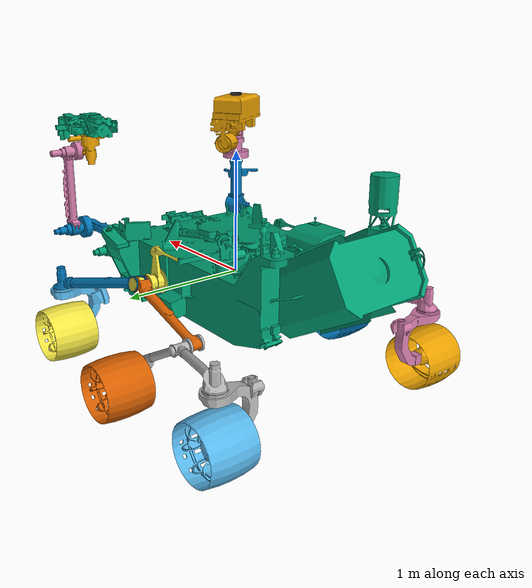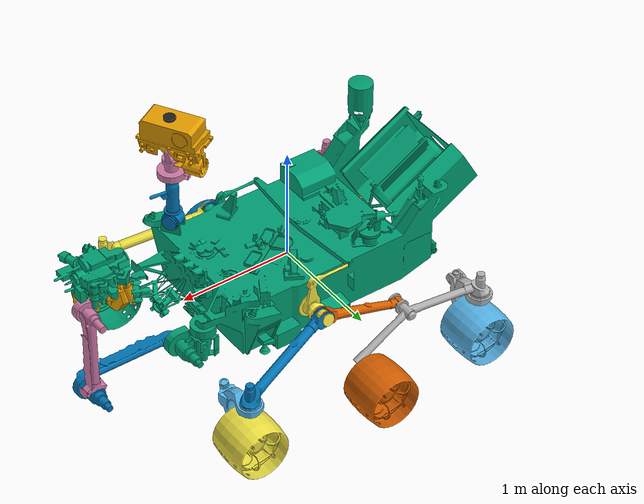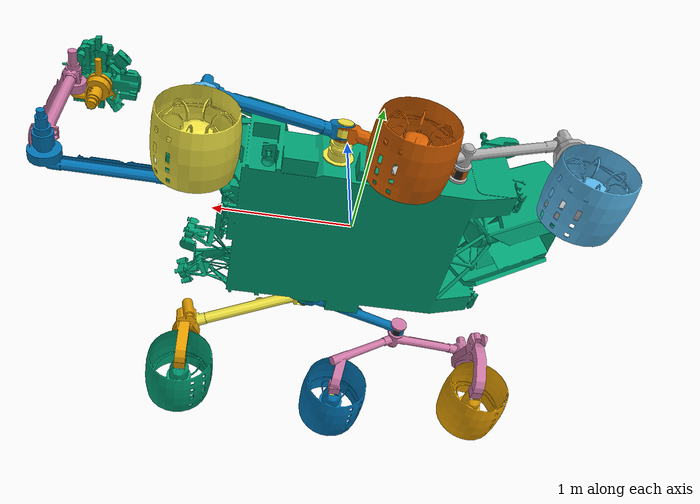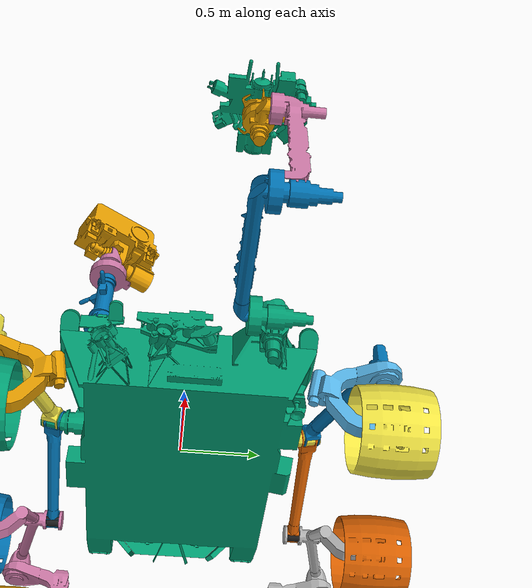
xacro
<?xml version="1.0"?>
<robot name="curiosity_mars_rover"
	xmlns:xacro="http://wiki.ros.org/xacro">

	<!-- Inertia matrices -->
	<xacro:include filename="$(find curiosity_description)/models/urdf/macros.xacro" />
	<!-- Robot constants and properties -->
	<xacro:include filename="$(find curiosity_description)/models/urdf/curiosity_mars_rover_properties.xacro" />
	<!-- Gazebo aspects of the robot -->
	<xacro:include filename="$(find curiosity_description)/models/urdf/curiosity_mars_rover.gazebo" />
	<!-- Chasis -->
	<xacro:include filename="$(find curiosity_description)/models/urdf/chassis.xacro" />
	<!-- Wheel Groups -->
	<xacro:include filename="$(find curiosity_description)/models/urdf/wheel.xacro" />
	<xacro:include filename="$(find curiosity_description)/models/urdf/left_wheel_group.xacro" />
	<xacro:include filename="$(find curiosity_description)/models/urdf/right_wheel_group.xacro" />
	<!-- Arm -->
	<xacro:include filename="$(find curiosity_description)/models/urdf/arm.xacro" />
	<!-- Sensor Mast -->
	<xacro:include filename="$(find curiosity_description)/models/urdf/sensor_mast.xacro" />

	<xacro:chassis_body/>
	<xacro:left_wheel_tree/>
	<xacro:right_wheel_tree/>

	<xacro:arm/>
	<xacro:sensor_mast/>

</robot>

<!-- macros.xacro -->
<!--
	definitions of some macros for easier description of the robot
-->

<robot xmlns:xacro="http://wiki.ros.org/xacro">

  <xacro:macro name="cylinder_inertia" params="m r h">

    <inertia
          ixx="${m*(3*r*r+h*h)/12}"
    			ixy = "0"
    			ixz = "0"
    			iyy="${m*(3*r*r+h*h)/12}"
    			iyz = "0"
    			izz="${m*r*r/2}"
    />
  </xacro:macro>

  <xacro:macro name="box_inertia" params="m x y z">

    <inertia
          ixx="${m*(y*y+z*z)/12}"
    			ixy = "0"
    			ixz = "0"
    			iyy="${m*(x*x+z*z)/12}"
    			iyz = "0"
    			izz="${m*(x*x+y*y)/12}"
    />
  </xacro:macro>

  <xacro:macro name="sphere_inertia" params="m r">

    <inertia
          ixx="${2*m*r*r/5}"
    			ixy = "0"
    			ixz = "0"
    			iyy="${2*m*r*r/5}"
    			iyz = "0"
    			izz="${2*m*r*r/5}"
    />
  </xacro:macro>

</robot>

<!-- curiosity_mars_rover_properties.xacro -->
<robot xmlns:xacro="http://wiki.ros.org/xacro">

	<!-- Constants -->
	<xacro:property name="PI" value="3.1415926535897931"/>

	<!-- Scaling -->
	<xacro:property name="scale_XYZ" value="1.0"/>

	<!-- Chassis properties -->
	<xacro:property name="chassisMass" value="733.64"/>

	<xacro:property name="chassisHeight" value="0.76"/>
	<xacro:property name="chassisLength" value="2.08157"/>
	<xacro:property name="chassisWidth" value="1.53774"/>

	<!-- Wheel Trees -->
	<xacro:property name="TreeMass" value="${72.96/2.0}"/>
	<xacro:property name="TreeParts" value="5.0"/>

	<xacro:property name="axisHeight" value="0.36388"/>
	<xacro:property name="axisLength" value="0.20321"/>
	<xacro:property name="axisWidth" value="0.27070"/>
	<xacro:property name="axisMass" value="${TreeMass/TreeParts}"/>

	<xacro:property name="suspension_arm_F_L_Mass" value="${TreeMass/TreeParts}"/>
	<xacro:property name="suspension_arm_F_L_X" value="0.39606"/>
	<xacro:property name="suspension_arm_F_L_Y" value="1.02203"/>
	<xacro:property name="suspension_arm_F_L_Z" value="0.30536"/>
	<xacro:property name="suspension_arm_F_L_limit" value="0.4"/>

	<xacro:property name="suspension_arm_B_L_Mass" value="${TreeMass/TreeParts}"/>
	<xacro:property name="suspension_arm_B_L_X" value="0.123524"/>
	<xacro:property name="suspension_arm_B_L_Y" value="0.852108"/>
	<xacro:property name="suspension_arm_B_L_Z" value="0.348354"/>
	<xacro:property name="suspension_arm_B_L_limit" value="0.4"/>

	<xacro:property name="suspension_arm_B2_L_Mass" value="${TreeMass/TreeParts}"/>
	<xacro:property name="suspension_arm_B2_L_X" value="0.400262"/>
	<xacro:property name="suspension_arm_B2_L_Y" value="1.22113"/>
	<xacro:property name="suspension_arm_B2_L_Z" value="0.631338"/>
	<xacro:property name="suspension_arm_B2_lower_limit" value="-1.2"/>
	<xacro:property name="suspension_arm_B2_upper_limit" value="1.2"/>

	<xacro:property name="suspension_steer_F_L_Mass" value="${TreeMass/TreeParts}"/>
	<xacro:property name="suspension_steer_F_L_X" value="0.528399"/>
	<xacro:property name="suspension_steer_F_L_Y" value="0.21019"/>
	<xacro:property name="suspension_steer_F_L_Z" value="0.450036"/>

	<xacro:property name="suspension_steer_B_L_Mass" value="${TreeMass/TreeParts}"/>
	<xacro:property name="suspension_steer_B_L_X" value="0.528399"/>
	<xacro:property name="suspension_steer_B_L_Y" value="0.21019"/>
	<xacro:property name="suspension_steer_B_L_Z" value="0.450036"/>

	<xacro:property name="suspension_steer_limit" value="0.6"/>
	<xacro:property name="suspension_steer_effort" value="10000.0"/>
	<xacro:property name="suspension_steer_velocity" value="10.0"/>

	<xacro:property name="suspension_effort" value="10000.0"/>
	<xacro:property name="suspension_speed" value="10.0"/>
	<xacro:property name="suspension_damping" value="0.5"/>
	<xacro:property name="suspension_friction" value="0.5"/>

	<!-- Wheels properties -->
	<xacro:property name="wheelWidth" value="0.39473"/>
	<xacro:property name="wheelRadius" value="0.242647"/>
	<xacro:property name="wheelMass" value="2.07"/>

	<!-- Arm -->
	<xacro:property name="armMass" value="30.0"/>
	<xacro:property name="armParts" value="5.0"/>

	<xacro:property name="arm_01_Mass" value="${armMass/armParts}"/>
	<xacro:property name="arm_01_X" value="0.356891"/>
	<xacro:property name="arm_01_Y" value="0.334128"/>
	<xacro:property name="arm_01_Z" value="0.300511"/>
	<xacro:property name="arm_01_limit" value="1.57"/>

	<xacro:property name="arm_02_Mass" value="${armMass/armParts}"/>
	<xacro:property name="arm_02_X" value="0.472171"/>
	<xacro:property name="arm_02_Y" value="0.972313"/>
	<xacro:property name="arm_02_Z" value="0.218611"/>
	<xacro:property name="arm_02_limit" value="1.57"/>

	<xacro:property name="arm_03_Mass" value="${armMass/armParts}"/>
	<xacro:property name="arm_03_X" value="0.30683"/>
	<xacro:property name="arm_03_Y" value="0.178607"/>
	<xacro:property name="arm_03_Z" value="0.878958"/>
	<xacro:property name="arm_03_limit" value="5.0"/>

	<xacro:property name="arm_04_Mass" value="${armMass/armParts}"/>
	<xacro:property name="arm_04_X" value="0.32452"/>
	<xacro:property name="arm_04_Y" value="0.344693"/>
	<xacro:property name="arm_04_Z" value="0.288832"/>
	<xacro:property name="arm_04_limit" value="1.57"/>

	<xacro:property name="arm_tools_Mass" value="${armMass/armParts}"/>
	<xacro:property name="arm_tools_X" value="0.60282"/>
	<xacro:property name="arm_tools_Y" value="0.467147"/>
	<xacro:property name="arm_tools_Z" value="0.21915"/>

	<!-- Mast -->
	<xacro:property name="mastMass" value="50.0"/>
	<xacro:property name="MastParts" value="3.0"/>

	<xacro:property name="mast_p_Mass" value="${mastMass/MastParts}"/>
	<xacro:property name="mast_p_X" value="0.192274"/>
	<xacro:property name="mast_p_Y" value="0.221494"/>
	<xacro:property name="mast_p_Z" value="0.525621"/>
	<xacro:property name="mast_p_upper_limit" value="1.57"/>
	<xacro:property name="mast_p_lower_limit" value="0.0"/>

	<xacro:property name="mast_02_Mass" value="${mastMass/MastParts}"/>
	<xacro:property name="mast_02_X" value="0.270963"/>
	<xacro:property name="mast_02_Y" value="0.232093"/>
	<xacro:property name="mast_02_Z" value="0.285976"/>

	<xacro:property name="mast_cameras_Mass" value="${mastMass/MastParts}"/>
	<xacro:property name="mast_cameras_X" value="0.550001"/>
	<xacro:property name="mast_cameras_Y" value="0.283001"/>
	<xacro:property name="mast_cameras_Z" value="0.203994"/>
	<xacro:property name="mast_cameras_limit" value="1.57"/>

</robot>

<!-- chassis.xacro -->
<robot xmlns:xacro="http://wiki.ros.org/xacro">

	<xacro:macro name="chassis_body" params="">

		<!-- Used for fixing robot to Gazebo 'chassis' -->
		<link name="base_footprint" />
		<link name="base_link" />

		<joint name="base_footprint_to_link" type="fixed">
			<parent link="base_footprint"/>
			<child link="base_link"/>
		</joint>

		<joint name="base_to_chassis" type="fixed">
			<parent link="base_link"/>
			<child link="chassis"/>
			<origin rpy="0 0 1.57" xyz="0 0 0"/>
		</joint>

		<link name='chassis'>

			<collision>
				<origin xyz="0 0 0" rpy="0 0 0"/>
				<geometry>
					<mesh filename="file://$(find curiosity_description)/models/meshes/chassis_full_fixed_glitch_v2.dae" scale="${scale_XYZ} ${scale_XYZ} ${scale_XYZ}"/>
				</geometry>
			</collision>

			<visual>
				<origin xyz="0 0 0" rpy="0 0 0"/>
				<geometry>
					<mesh filename="file://$(find curiosity_description)/models/meshes/chassis_full_fixed_glitch_v2.dae" scale="${scale_XYZ} ${scale_XYZ} ${scale_XYZ}"/>
				</geometry>
			</visual>

			<inertial>
				<origin xyz="0 0 0" rpy="0 0 0"/>
				<mass value="${chassisMass}"/>
				<xacro:box_inertia m="${chassisMass}" x="${chassisWidth*scale_XYZ}" y="${chassisLength*scale_XYZ}" z="${chassisHeight*scale_XYZ}"/>
			</inertial>

		</link>

	</xacro:macro>

</robot>

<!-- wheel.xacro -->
<robot xmlns:xacro="http://wiki.ros.org/xacro">

	<xacro:macro name="wheel" params="wheel_name wheel_conector_name tY">
		<!-- tY is Zero if left side, 1 if right side -->
		<link name='${wheel_name}'>
			<collision>
				<origin xyz="0 0 0" rpy="0 1.57 0"/>
				<geometry>
					<cylinder radius="${wheelRadius}" length="${wheelWidth}"/>
				</geometry>
			</collision>

			<visual>
				<origin xyz="0 0 0" rpy="0 0 0"/>
				<geometry>
					<mesh filename="file://$(find curiosity_description)/models/meshes/wheel_fixed.dae" scale="${scale_XYZ} ${scale_XYZ} ${scale_XYZ}"/>
				</geometry>
			</visual>

			<inertial>
				<origin xyz="0 0 0" rpy="0 0 0"/>
				<mass value="${wheelMass}"/>
				<xacro:cylinder_inertia m="${wheelMass}" r="${wheelRadius*scale_XYZ}" h="${wheelWidth*scale_XYZ}"/>
			</inertial>
		</link>

		<gazebo reference="${wheel_name}">
			<mu1 value="1.0"/>
			<mu2 value="1.0"/>
			<kp value="10000000.0" />
			<kd>100.0</kd>
			<minDepth>0.001</minDepth>
			<maxVel>1.0</maxVel>
		</gazebo>

		<joint name="${wheel_name}_joint" type="continuous">
			<parent link="${wheel_conector_name}"/>
			<child link="${wheel_name}"/>
			<origin xyz="0 0 0" rpy="0 0 ${tY*PI}"/>
			<limit effort="10000.0" velocity="100.0"/>
			<axis xyz="1 0 0"/>
			<dynamics damping="0.0" friction="0.0"/>
		</joint>

		<transmission name="${wheel_name}_trans">
			<type>transmission_interface/SimpleTransmission</type>
			<joint name="${wheel_name}_joint">
				<hardwareInterface>hardware_interface/EffortJointInterface</hardwareInterface>
			</joint>
			<actuator name="${wheel_name}Motor">
				<hardwareInterface>hardware_interface/EffortJointInterface</hardwareInterface>
				<mechanicalReduction>1</mechanicalReduction>
			</actuator>
		</transmission>

	</xacro:macro>

</robot>

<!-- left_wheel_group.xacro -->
<robot xmlns:xacro="http://wiki.ros.org/xacro">

	<xacro:macro name="left_wheel_tree" params="">

		<link name='left_axis'>

			<collision>
				<origin xyz="0 0 0" rpy="0 0 0"/>
				<geometry>
					<mesh filename="file://$(find curiosity_description)/models/meshes/left_axis_jointfix_v2.dae" scale="${scale_XYZ} ${scale_XYZ} ${scale_XYZ}"/>
				</geometry>
			</collision>

			<visual>
				<origin xyz="0 0 0" rpy="0 0 0"/>
				<geometry>
					<mesh filename="file://$(find curiosity_description)/models/meshes/left_axis_jointfix_v2.dae" scale="${scale_XYZ} ${scale_XYZ} ${scale_XYZ}"/>
				</geometry>
			</visual>

			<inertial>
				<origin xyz="0 0 0" rpy="0 0 0"/>
				<mass value="${axisMass}"/>
				<xacro:box_inertia m="${axisMass}" x="${axisWidth*scale_XYZ}" y="${axisLength*scale_XYZ}" z="${axisHeight*scale_XYZ}"/>
			</inertial>

		</link>

		<joint name="left_axis_joint" type="fixed">
			<parent link="chassis"/>
			<child link="left_axis"/>
			<origin xyz="0.7938 -0.2133 0" rpy="0 -0.19565141 0"/>
		</joint>

		<link name='suspension_arm_F_L'>
			<collision>
				<origin xyz="0 0 0" rpy="0 0 0"/>
				<geometry>
					<mesh filename="file://$(find curiosity_description)/models/meshes/suspension_arm_F_L_fixed.dae" scale="${scale_XYZ} ${scale_XYZ} ${scale_XYZ}"/>
				</geometry>
			</collision>

			<visual>
				<origin xyz="0 0 0" rpy="0 0 0"/>
				<geometry>
					<mesh filename="file://$(find curiosity_description)/models/meshes/suspension_arm_F_L_fixed.dae" scale="${scale_XYZ} ${scale_XYZ} ${scale_XYZ}"/>
				</geometry>
			</visual>

			<inertial>
				<origin xyz="0 0 0" rpy="0 0 0"/>
				<mass value="${suspension_arm_F_L_Mass}"/>
				<xacro:box_inertia m="${suspension_arm_F_L_Mass}" x="${suspension_arm_F_L_X*scale_XYZ}" y="${suspension_arm_F_L_Y*scale_XYZ}" z="${suspension_arm_F_L_Z*scale_XYZ}"/>
			</inertial>
		</link>

		<joint name="suspension_arm_F_L_joint" type="revolute">
			<parent link="left_axis"/>
			<child link="suspension_arm_F_L"/>
			<origin xyz="0 0 0" rpy="0 0 0"/>
			<limit lower="${-suspension_arm_F_L_limit}" upper="${suspension_arm_F_L_limit}" effort="${suspension_effort}" velocity="${suspension_speed}"/>
			<axis xyz="1 0 0"/>
			<dynamics damping="${suspension_damping}" friction="${suspension_friction}"/>
		</joint>

		<transmission name="suspension_arm_F_L_trans">
			<type>transmission_interface/SimpleTransmission</type>
			<joint name="suspension_arm_F_L_joint">
				<hardwareInterface>hardware_interface/EffortJointInterface</hardwareInterface>
			</joint>
			<actuator name="suspension_arm_F_LMotor">
				<hardwareInterface>hardware_interface/EffortJointInterface</hardwareInterface>
				<mechanicalReduction>1</mechanicalReduction>
			</actuator>
		</transmission>

		<link name='suspension_arm_B_L'>
			<collision>
				<origin xyz="0 0 0" rpy="0 0 0"/>
				<geometry>
					<mesh filename="file://$(find curiosity_description)/models/meshes/suspension_arm_B_L_fixed.dae" scale="${scale_XYZ} ${scale_XYZ} ${scale_XYZ}"/>
				</geometry>
			</collision>

			<visual>
				<origin xyz="0 0 0" rpy="0 0 0"/>
				<geometry>
					<mesh filename="file://$(find curiosity_description)/models/meshes/suspension_arm_B_L_fixed.dae" scale="${scale_XYZ} ${scale_XYZ} ${scale_XYZ}"/>
				</geometry>
			</visual>

			<inertial>
				<origin xyz="0 0 0" rpy="0 0 0"/>
				<mass value="${suspension_arm_B_L_Mass}"/>
				<xacro:box_inertia m="${suspension_arm_B_L_Mass}" x="${suspension_arm_B_L_X*scale_XYZ}" y="${suspension_arm_B_L_Y*scale_XYZ}" z="${suspension_arm_B_L_Z*scale_XYZ}"/>
			</inertial>
		</link>

		<joint name="suspension_arm_B_L_joint" type="revolute">
			<parent link="left_axis"/>
			<child link="suspension_arm_B_L"/>
			<origin xyz="0 0 0" rpy="0 0 0"/>
			<limit lower="${-suspension_arm_B_L_limit}" upper="${suspension_arm_B_L_limit}" effort="${suspension_effort}" velocity="${suspension_speed}"/>
			<axis xyz="1 0 0"/>
			<dynamics damping="${suspension_damping}" friction="${suspension_friction}"/>
		</joint>

		<transmission name="suspension_arm_B_L_trans">
			<type>transmission_interface/SimpleTransmission</type>
			<joint name="suspension_arm_B_L_joint">
				<hardwareInterface>hardware_interface/EffortJointInterface</hardwareInterface>
			</joint>
			<actuator name="suspension_arm_B_LMotor">
				<hardwareInterface>hardware_interface/EffortJointInterface</hardwareInterface>
				<mechanicalReduction>1</mechanicalReduction>
			</actuator>
		</transmission>

		<link name='suspension_arm_B_L_to_B2_L'>
			<inertial>
				<origin xyz="0 0 0" rpy="0 0 0"/>
				<mass value="0.02" />
				<inertia ixx="2.61666666667e-05" ixy="0.0" ixz="0.0" iyy="2.61666666667e-05" iyz="0.0" izz="3.6e-05"/>
			</inertial>
			<collision>
				<origin xyz="0 0 0.015" rpy="0 0 0"/>
				<geometry>
					<cylinder radius="0.06" length="0.035"/>
				</geometry>
			</collision>
			<visual>
				<origin rpy="0.0 1.57 0" xyz="0 0 0"/>
				<geometry>
					<cylinder radius="0.04" length="0.1"/>
				</geometry>
			</visual>
		</link>

		<joint name="suspension_arm_B_L_to_B2_L_joint" type="fixed">
			<parent link="suspension_arm_B_L"/>
			<child link="suspension_arm_B_L_to_B2_L"/>
			<origin xyz="-0.05159 0.73683 -0.22972" rpy="0 0.1937315 0"/>
		</joint>

		<link name='suspension_arm_B2_L'>
			<collision>
				<origin xyz="0 0 0" rpy="0 0 0"/>
				<geometry>
					<mesh filename="file://$(find curiosity_description)/models/meshes/suspension_arm_B2_L_fixed.dae" scale="${scale_XYZ} ${scale_XYZ} ${scale_XYZ}"/>
				</geometry>
			</collision>

			<visual>
				<origin xyz="0 0 0" rpy="0 0 0"/>
				<geometry>
					<mesh filename="file://$(find curiosity_description)/models/meshes/suspension_arm_B2_L_fixed.dae" scale="${scale_XYZ} ${scale_XYZ} ${scale_XYZ}"/>
				</geometry>
			</visual>

			<inertial>
				<origin xyz="0 0 0" rpy="0 0 0"/>
				<mass value="${suspension_arm_B2_L_Mass}"/>
				<xacro:box_inertia m="${suspension_arm_B2_L_Mass}" x="${suspension_arm_B2_L_X*scale_XYZ}" y="${suspension_arm_B2_L_Y*scale_XYZ}" z="${suspension_arm_B2_L_Z*scale_XYZ}"/>
			</inertial>
		</link>

		<joint name="suspension_arm_B2_L_joint" type="revolute">
			<parent link="suspension_arm_B_L_to_B2_L"/>
			<child link="suspension_arm_B2_L"/>
			<origin xyz="0 0 0" rpy="0 0 0"/>
			<limit lower="${suspension_arm_B2_lower_limit}" upper="${suspension_arm_B2_upper_limit}" effort="${suspension_effort}" velocity="${suspension_speed}"/>
			<axis xyz="1 0 0"/>
			<dynamics damping="${suspension_damping}" friction="${suspension_friction}"/>
		</joint>

		<transmission name="suspension_arm_B2_L_trans">
			<type>transmission_interface/SimpleTransmission</type>
			<joint name="suspension_arm_B2_L_joint">
				<hardwareInterface>hardware_interface/EffortJointInterface</hardwareInterface>
			</joint>
			<actuator name="suspension_arm_B2_LMotor">
				<hardwareInterface>hardware_interface/EffortJointInterface</hardwareInterface>
				<mechanicalReduction>1</mechanicalReduction>
			</actuator>
		</transmission>

		<!-- FRONT WHEEL -->
		<link name='suspension_arm_F_L_to_suspension_steer_F_L'>
			<inertial>
				<origin xyz="0 0 0" rpy="0 0 0"/>
				<mass value="0.02" />
				<inertia ixx="2.61666666667e-05" ixy="0.0" ixz="0.0" iyy="2.61666666667e-05" iyz="0.0" izz="3.6e-05"/>
			</inertial>
			<collision>
				<origin xyz="0 0 0.015" rpy="0 0 0"/>
				<geometry>
					<cylinder radius="0.06" length="0.04"/>
				</geometry>
			</collision>
			<visual>
				<origin rpy="0.0 0 0" xyz="0 0 0"/>
				<geometry>
					<cylinder radius="0.06" length="0.04"/>
				</geometry>
			</visual>
		</link>

		<joint name="suspension_arm_F_L_to_suspension_steer_F_L_joint" type="fixed">
			<parent link="suspension_arm_F_L"/>
			<child link="suspension_arm_F_L_to_suspension_steer_F_L"/>
			<origin xyz="0.2057 -0.87876 -0.29370" rpy="0 0.1937315 0"/>
		</joint>

		<link name='suspension_steer_F_L'>
			<collision>
				<origin xyz="0 0 0" rpy="0 0 0"/>
				<geometry>
					<mesh filename="file://$(find curiosity_description)/models/meshes/suspension_steer_F_L_fixed.dae" scale="${scale_XYZ} ${scale_XYZ} ${scale_XYZ}"/>
				</geometry>
			</collision>

			<visual>
				<origin xyz="0 0 0" rpy="0 0 0"/>
				<geometry>
					<mesh filename="file://$(find curiosity_description)/models/meshes/suspension_steer_F_L_fixed.dae" scale="${scale_XYZ} ${scale_XYZ} ${scale_XYZ}"/>
				</geometry>
			</visual>

			<inertial>
				<origin xyz="0 0 0" rpy="0 0 0"/>
				<mass value="${suspension_steer_F_L_Mass}"/>
				<xacro:box_inertia m="${suspension_steer_F_L_Mass}" x="${suspension_steer_F_L_X*scale_XYZ}" y="${suspension_steer_F_L_Y*scale_XYZ}" z="${suspension_steer_F_L_Z*scale_XYZ}"/>
			</inertial>
		</link>

		<joint name="suspension_steer_F_L_joint" type="revolute">
			<parent link="suspension_arm_F_L_to_suspension_steer_F_L"/>
			<child link="suspension_steer_F_L"/>
			<origin xyz="0 0 0" rpy="0 0 0"/>
			<limit lower="${-suspension_steer_limit}" upper="${suspension_steer_limit}" effort="${suspension_steer_effort}" velocity="${suspension_steer_velocity}"/>
			<axis xyz="0 0 1"/>
		</joint>

		<transmission name="suspension_steer_F_L_trans">
			<type>transmission_interface/SimpleTransmission</type>
			<joint name="suspension_steer_F_L_joint">
				<hardwareInterface>hardware_interface/EffortJointInterface</hardwareInterface>
			</joint>
			<actuator name="suspension_steer_F_LMotor">
				<hardwareInterface>hardware_interface/EffortJointInterface</hardwareInterface>
				<mechanicalReduction>1</mechanicalReduction>
			</actuator>
		</transmission>

		<link name='suspension_steer_F_L_to_front_wheel_L'>
			<inertial>
				<origin xyz="0 0 0" rpy="0 0 0"/>
				<mass value="0.02" />
				<inertia ixx="2.61666666667e-05" ixy="0.0" ixz="0.0" iyy="2.61666666667e-05" iyz="0.0" izz="3.6e-05"/>
			</inertial>
			<collision>
				<origin rpy="0.0 1.57 0" xyz="0 0 0"/>
				<geometry>
					<cylinder radius="0.02" length="0.02"/>
				</geometry>
			</collision>
			<visual>
				<origin rpy="0.0 1.57 0" xyz="0 0 0"/>
				<geometry>
					<cylinder radius="0.02" length="0.02"/>
				</geometry>
			</visual>
		</link>

		<joint name="suspension_steer_F_L_to_suspension_steer_F_L_to_front_wheel_L_joint" type="fixed">
			<parent link="suspension_steer_F_L"/>
			<child link="suspension_steer_F_L_to_front_wheel_L"/>
			<origin xyz="0 0 -0.3996" rpy="0 0 0"/>
		</joint>

		<xacro:wheel wheel_name="front_wheel_L" wheel_conector_name="suspension_steer_F_L_to_front_wheel_L" tY="0"/>

		<!-- FRONT LEFT Wheel Left END -->

		<!-- MIDDLE WHEEL -->

		<link name='suspension_arm_B2_L_to_middle_wheel_L'>
			<inertial>
				<origin xyz="0 0 0" rpy="0 0 0"/>
				<mass value="0.02" />
				<inertia ixx="2.61666666667e-05" ixy="0.0" ixz="0.0" iyy="2.61666666667e-05" iyz="0.0" izz="3.6e-05"/>
			</inertial>
			<collision>
				<origin rpy="0.0 1.57 0" xyz="0 0 0"/>
				<geometry>
					<cylinder radius="0.02" length="0.02"/>
				</geometry>
			</collision>
			<visual>
				<origin rpy="0.0 1.57 0" xyz="0 0 0"/>
				<geometry>
					<cylinder radius="0.02" length="0.02"/>
				</geometry>
			</visual>
		</link>

		<joint name="suspension_arm_B2_L_to_suspension_arm_B2_L_to_middle_wheel_L_joint" type="fixed">
			<parent link="suspension_arm_B2_L"/>
			<child link="suspension_arm_B2_L_to_middle_wheel_L"/>
			<origin xyz="0.39423 -0.44859 -0.41098" rpy="0 0 0"/>
		</joint>

		<xacro:wheel wheel_name="middle_wheel_L" wheel_conector_name="suspension_arm_B2_L_to_middle_wheel_L" tY="0"/>

		<!-- FRONT MIDDLE Wheel Left END -->

		<!-- BACK WHEEL -->
		<link name='suspension_arm_B2_L_to_suspension_steer_B_L'>
			<inertial>
				<origin xyz="0 0 0" rpy="0 0 0"/>
				<mass value="0.02" />
				<inertia ixx="2.61666666667e-05" ixy="0.0" ixz="0.0" iyy="2.61666666667e-05" iyz="0.0" izz="3.6e-05"/>
			</inertial>
			<collision>
				<origin xyz="0 0 0.015" rpy="0 0 0"/>
				<geometry>
					<cylinder radius="0.06" length="0.04"/>
				</geometry>
			</collision>
			<visual>
				<origin rpy="0.0 0 0" xyz="0 0 0"/>
				<geometry>
					<cylinder radius="0.06" length="0.04"/>
				</geometry>
			</visual>
		</link>

		<joint name="suspension_arm_B2_L_to_suspension_steer_B_L_joint" type="fixed">
			<parent link="suspension_arm_B2_L"/>
			<child link="suspension_arm_B2_L_to_suspension_steer_B_L"/>
			<origin xyz="0.26271 0.62363 -0.00069" rpy="0 0 0"/>
		</joint>

		<link name='suspension_steer_B_L'>
			<collision>
				<origin xyz="0 0 0" rpy="0 0 0"/>
				<geometry>
					<mesh filename="file://$(find curiosity_description)/models/meshes/suspension_steer_B_L_fixed.dae" scale="${scale_XYZ} ${scale_XYZ} ${scale_XYZ}"/>
				</geometry>
			</collision>

			<visual>
				<origin xyz="0 0 0" rpy="0 0 0"/>
				<geometry>
					<mesh filename="file://$(find curiosity_description)/models/meshes/suspension_steer_B_L_fixed.dae" scale="${scale_XYZ} ${scale_XYZ} ${scale_XYZ}"/>
				</geometry>
			</visual>

			<inertial>
				<origin xyz="0 0 0" rpy="0 0 0"/>
				<mass value="${suspension_steer_B_L_Mass}"/>
				<xacro:box_inertia m="${suspension_steer_B_L_Mass}" x="${suspension_steer_B_L_X*scale_XYZ}" y="${suspension_steer_B_L_Y*scale_XYZ}" z="${suspension_steer_B_L_Z*scale_XYZ}"/>
			</inertial>
		</link>

		<joint name="suspension_steer_B_L_joint" type="revolute">
			<parent link="suspension_arm_B2_L_to_suspension_steer_B_L"/>
			<child link="suspension_steer_B_L"/>
			<origin xyz="0 0 0" rpy="0 0 0"/>
			<limit lower="${-suspension_steer_limit}" upper="${suspension_steer_limit}" effort="${suspension_steer_effort}" velocity="${suspension_steer_velocity}"/>
			<axis xyz="0 0 1"/>
		</joint>

		<transmission name="suspension_steer_B_L_trans">
			<type>transmission_interface/SimpleTransmission</type>
			<joint name="suspension_steer_B_L_joint">
				<hardwareInterface>hardware_interface/EffortJointInterface</hardwareInterface>
			</joint>
			<actuator name="suspension_steer_B_LMotor">
				<hardwareInterface>hardware_interface/EffortJointInterface</hardwareInterface>
				<mechanicalReduction>1</mechanicalReduction>
			</actuator>
		</transmission>

		<link name='suspension_steer_B_L_to_back_wheel_L'>
			<inertial>
				<origin xyz="0 0 0" rpy="0 0 0"/>
				<mass value="0.02" />
				<inertia ixx="2.61666666667e-05" ixy="0.0" ixz="0.0" iyy="2.61666666667e-05" iyz="0.0" izz="3.6e-05"/>
			</inertial>
			<collision>
				<origin rpy="0.0 1.57 0" xyz="0 0 0"/>
				<geometry>
					<cylinder radius="0.02" length="0.02"/>
				</geometry>
			</collision>
			<visual>
				<origin rpy="0.0 1.57 0" xyz="0 0 0"/>
				<geometry>
					<cylinder radius="0.02" length="0.02"/>
				</geometry>
			</visual>
		</link>

		<joint name="suspension_arm_B2_L_to_suspension_steer_B_L_to_back_wheel_L_joint" type="fixed">
			<parent link="suspension_steer_B_L"/>
			<child link="suspension_steer_B_L_to_back_wheel_L"/>
			<origin xyz="0 0 -0.410523" rpy="0 0 0"/>
		</joint>

		<xacro:wheel wheel_name="back_wheel_L" wheel_conector_name="suspension_steer_B_L_to_back_wheel_L" tY="0"/>

		<!-- END BACK WHEEL LEFT -->
	</xacro:macro>

</robot>

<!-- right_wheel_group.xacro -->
<robot xmlns:xacro="http://wiki.ros.org/xacro">

	<xacro:macro name="right_wheel_tree" params="">

		<link name='right_axis'>
			<collision>
				<origin xyz="0 0 0" rpy="0 0 0"/>
				<geometry>
					<mesh filename="file://$(find curiosity_description)/models/meshes/right_axis_jointfix_v2.dae" scale="${scale_XYZ} ${scale_XYZ} ${scale_XYZ}"/>
				</geometry>
			</collision>

			<visual>
				<origin xyz="0 0 0" rpy="0 0 0"/>
				<geometry>
					<mesh filename="file://$(find curiosity_description)/models/meshes/right_axis_jointfix_v2.dae" scale="${scale_XYZ} ${scale_XYZ} ${scale_XYZ}"/>
				</geometry>
			</visual>

			<inertial>
				<origin xyz="0 0 0" rpy="0 0 0"/>
				<mass value="${axisMass}"/>
				<xacro:box_inertia m="${axisMass}" x="${axisWidth*scale_XYZ}" y="${axisLength*scale_XYZ}" z="${axisHeight*scale_XYZ}"/>
			</inertial>
		</link>

		<joint name="right_axis_joint" type="fixed">
			<parent link="chassis"/>
			<child link="right_axis"/>
			<origin xyz="-0.7938 -0.2133 0" rpy="0 0.19565141 0"/>
		</joint>

		<link name='suspension_arm_F_R'>
			<collision>
				<origin xyz="0 0 0" rpy="0 0 0"/>
				<geometry>
					<mesh filename="file://$(find curiosity_description)/models/meshes/suspension_arm_F_R_fixed.dae" scale="${scale_XYZ} ${scale_XYZ} ${scale_XYZ}"/>
				</geometry>
			</collision>

			<visual>
				<origin xyz="0 0 0" rpy="0 0 0"/>
				<geometry>
					<mesh filename="file://$(find curiosity_description)/models/meshes/suspension_arm_F_R_fixed.dae" scale="${scale_XYZ} ${scale_XYZ} ${scale_XYZ}"/>
				</geometry>
			</visual>

			<inertial>
				<origin xyz="0 0 0" rpy="0 0 0"/>
				<mass value="${suspension_arm_F_L_Mass}"/>
				<xacro:box_inertia m="${suspension_arm_F_L_Mass}" x="${suspension_arm_F_L_X*scale_XYZ}" y="${suspension_arm_F_L_Y*scale_XYZ}" z="${suspension_arm_F_L_Z*scale_XYZ}"/>
			</inertial>
		</link>

		<joint name="suspension_arm_F_R_joint" type="revolute">
			<parent link="right_axis"/>
			<child link="suspension_arm_F_R"/>
			<origin xyz="0 0 0" rpy="0 0 0"/>
			<limit lower="${-suspension_arm_F_L_limit}" upper="${suspension_arm_F_L_limit}" effort="${suspension_effort}" velocity="${suspension_speed}"/>
			<axis xyz="1 0 0"/>
			<dynamics damping="${suspension_damping}" friction="${suspension_friction}"/>
		</joint>

		<transmission name="suspension_arm_F_R_trans">
			<type>transmission_interface/SimpleTransmission</type>
			<joint name="suspension_arm_F_R_joint">
				<hardwareInterface>hardware_interface/EffortJointInterface</hardwareInterface>
			</joint>
			<actuator name="suspension_arm_F_RMotor">
				<hardwareInterface>hardware_interface/EffortJointInterface</hardwareInterface>
				<mechanicalReduction>1</mechanicalReduction>
			</actuator>
		</transmission>

		<link name='suspension_arm_B_R'>
			<collision>
				<origin xyz="0 0 0" rpy="0 0 0"/>
				<geometry>
					<mesh filename="file://$(find curiosity_description)/models/meshes/suspension_arm_B_R_fixed.dae" scale="${scale_XYZ} ${scale_XYZ} ${scale_XYZ}"/>
				</geometry>
			</collision>

			<visual>
				<origin xyz="0 0 0" rpy="0 0 0"/>
				<geometry>
					<mesh filename="file://$(find curiosity_description)/models/meshes/suspension_arm_B_R_fixed.dae" scale="${scale_XYZ} ${scale_XYZ} ${scale_XYZ}"/>
				</geometry>
			</visual>

			<inertial>
				<origin xyz="0 0 0" rpy="0 0 0"/>
				<mass value="${suspension_arm_B_L_Mass}"/>
				<xacro:box_inertia m="${suspension_arm_B_L_Mass}" x="${suspension_arm_B_L_X*scale_XYZ}" y="${suspension_arm_B_L_Y*scale_XYZ}" z="${suspension_arm_B_L_Z*scale_XYZ}"/>
			</inertial>
		</link>

		<joint name="suspension_arm_B_R_joint" type="revolute">
			<parent link="right_axis"/>
			<child link="suspension_arm_B_R"/>
			<origin xyz="0 0 0" rpy="0 0 0"/>
			<limit lower="${-suspension_arm_B_L_limit}" upper="${suspension_arm_B_L_limit}" effort="${suspension_effort}" velocity="${suspension_speed}"/>
			<axis xyz="1 0 0"/>
			<dynamics damping="${suspension_damping}" friction="${suspension_friction}"/>
		</joint>

		<transmission name="suspension_arm_B_R_trans">
			<type>transmission_interface/SimpleTransmission</type>
			<joint name="suspension_arm_B_R_joint">
				<hardwareInterface>hardware_interface/EffortJointInterface</hardwareInterface>
			</joint>
			<actuator name="suspension_arm_B_RMotor">
				<hardwareInterface>hardware_interface/EffortJointInterface</hardwareInterface>
				<mechanicalReduction>1</mechanicalReduction>
			</actuator>
		</transmission>

		<link name='suspension_arm_B_R_to_B2_R'>
			<inertial>
				<origin xyz="0 0 0" rpy="0 0 0"/>
				<mass value="0.02" />
				<inertia ixx="2.61666666667e-05" ixy="0.0" ixz="0.0" iyy="2.61666666667e-05" iyz="0.0" izz="3.6e-05"/>
			</inertial>
			<collision>
				<origin xyz="0 0 0.015" rpy="0 0 0"/>
				<geometry>
					<cylinder radius="0.06" length="0.035"/>
				</geometry>
			</collision>
			<visual>
				<origin rpy="0.0 1.57 0" xyz="0 0 0"/>
				<geometry>
					<cylinder radius="0.04" length="0.1"/>
				</geometry>
			</visual>
		</link>

		<joint name="suspension_arm_B_R_to_B2_R_joint" type="fixed">
			<parent link="suspension_arm_B_R"/>
			<child link="suspension_arm_B_R_to_B2_R"/>
			<origin xyz="0.05159 0.73683 -0.22972" rpy="0 -0.1937315 0"/>
		</joint>

		<link name='suspension_arm_B2_R'>
			<collision>
				<origin xyz="0 0 0" rpy="0 0 0"/>
				<geometry>
					<mesh filename="file://$(find curiosity_description)/models/meshes/suspension_arm_B2_R_fixed.dae" scale="${scale_XYZ} ${scale_XYZ} ${scale_XYZ}"/>
				</geometry>
			</collision>

			<visual>
				<origin xyz="0 0 0" rpy="0 0 0"/>
				<geometry>
					<mesh filename="file://$(find curiosity_description)/models/meshes/suspension_arm_B2_R_fixed.dae" scale="${scale_XYZ} ${scale_XYZ} ${scale_XYZ}"/>
				</geometry>
			</visual>

			<inertial>
				<origin xyz="0 0 0" rpy="0 0 0"/>
				<mass value="${suspension_arm_B2_L_Mass}"/>
				<xacro:box_inertia m="${suspension_arm_B2_L_Mass}" x="${suspension_arm_B2_L_X*scale_XYZ}" y="${suspension_arm_B2_L_Y*scale_XYZ}" z="${suspension_arm_B2_L_Z*scale_XYZ}"/>
			</inertial>
		</link>

		<joint name="suspension_arm_B2_R_joint" type="revolute">
			<parent link="suspension_arm_B_R_to_B2_R"/>
			<child link="suspension_arm_B2_R"/>
			<origin xyz="0 0 0" rpy="0 0 0"/>
			<limit lower="${suspension_arm_B2_lower_limit}" upper="${suspension_arm_B2_upper_limit}" effort="${suspension_effort}" velocity="${suspension_speed}"/>
			<axis xyz="1 0 0"/>
			<dynamics damping="${suspension_damping}" friction="${suspension_friction}"/>
		</joint>

		<transmission name="suspension_arm_B2_R_trans">
			<type>transmission_interface/SimpleTransmission</type>
			<joint name="suspension_arm_B2_R_joint">
				<hardwareInterface>hardware_interface/EffortJointInterface</hardwareInterface>
			</joint>
			<actuator name="suspension_arm_B2_RMotor">
				<hardwareInterface>hardware_interface/EffortJointInterface</hardwareInterface>
				<mechanicalReduction>1</mechanicalReduction>
			</actuator>
		</transmission>

		<!-- FRONT WHEEL RIGHT -->

		<link name='suspension_arm_F_R_to_suspension_steer_F_R'>
			<inertial>
				<origin xyz="0 0 0" rpy="0 0 0"/>
				<mass value="0.02" />
				<inertia ixx="2.61666666667e-05" ixy="0.0" ixz="0.0" iyy="2.61666666667e-05" iyz="0.0" izz="3.6e-05"/>
			</inertial>
			<collision>
				<origin xyz="0 0 0.015" rpy="0 0 0"/>
				<geometry>
					<cylinder radius="0.06" length="0.04"/>
				</geometry>
			</collision>
			<visual>
				<origin rpy="0.0 0 0" xyz="0 0 0"/>
				<geometry>
					<cylinder radius="0.06" length="0.04"/>
				</geometry>
			</visual>
		</link>

		<joint name="suspension_arm_F_R_to_suspension_steer_F_R_joint" type="fixed">
			<parent link="suspension_arm_F_R"/>
			<child link="suspension_arm_F_R_to_suspension_steer_F_R"/>
			<origin xyz="-0.2057 -0.87876 -0.29370" rpy="0 -0.1937315 0"/>
		</joint>

		<link name='suspension_steer_F_R'>
			<collision>
				<origin xyz="0 0 0" rpy="0 0 0"/>
				<geometry>
					<mesh filename="file://$(find curiosity_description)/models/meshes/suspension_steer_F_R_fixed.dae" scale="${scale_XYZ} ${scale_XYZ} ${scale_XYZ}"/>
				</geometry>
			</collision>

			<visual>
				<origin xyz="0 0 0" rpy="0 0 0"/>
				<geometry>
					<mesh filename="file://$(find curiosity_description)/models/meshes/suspension_steer_F_R_fixed.dae" scale="${scale_XYZ} ${scale_XYZ} ${scale_XYZ}"/>
				</geometry>
			</visual>

			<inertial>
				<origin xyz="0 0 0" rpy="0 0 0"/>
				<mass value="${suspension_steer_F_L_Mass}"/>
				<xacro:box_inertia m="${suspension_steer_F_L_Mass}" x="${suspension_steer_F_L_X*scale_XYZ}" y="${suspension_steer_F_L_Y*scale_XYZ}" z="${suspension_steer_F_L_Z*scale_XYZ}"/>
			</inertial>
		</link>

		<joint name="suspension_steer_F_R_joint" type="revolute">
			<parent link="suspension_arm_F_R_to_suspension_steer_F_R"/>
			<child link="suspension_steer_F_R"/>
			<origin xyz="0 0 0" rpy="0 0 0"/>
			<limit lower="${-suspension_steer_limit}" upper="${suspension_steer_limit}" effort="${suspension_steer_effort}" velocity="${suspension_steer_velocity}"/>
			<axis xyz="0 0 1"/>
		</joint>

		<transmission name="suspension_steer_F_R_trans">
			<type>transmission_interface/SimpleTransmission</type>
			<joint name="suspension_steer_F_R_joint">
				<hardwareInterface>hardware_interface/EffortJointInterface</hardwareInterface>
			</joint>
			<actuator name="suspension_steer_F_RMotor">
				<hardwareInterface>hardware_interface/EffortJointInterface</hardwareInterface>
				<mechanicalReduction>1</mechanicalReduction>
			</actuator>
		</transmission>

		<link name='suspension_steer_F_R_to_front_wheel_R'>
			<inertial>
				<origin xyz="0 0 0" rpy="0 0 0"/>
				<mass value="0.02" />
				<inertia ixx="2.61666666667e-05" ixy="0.0" ixz="0.0" iyy="2.61666666667e-05" iyz="0.0" izz="3.6e-05"/>
			</inertial>
			<collision>
				<origin rpy="0.0 1.57 0" xyz="0 0 0"/>
				<geometry>
					<cylinder radius="0.02" length="0.02"/>
				</geometry>
			</collision>
			<visual>
				<origin rpy="0.0 1.57 0" xyz="0 0 0"/>
				<geometry>
					<cylinder radius="0.02" length="0.02"/>
				</geometry>
			</visual>
		</link>

		<joint name="suspension_steer_F_R_to_suspension_steer_F_R_to_front_wheel_R_joint" type="fixed">
			<parent link="suspension_steer_F_R"/>
			<child link="suspension_steer_F_R_to_front_wheel_R"/>
			<origin xyz="0 0 -0.3996" rpy="0 0 0"/>
		</joint>

		<xacro:wheel wheel_name="front_wheel_R" wheel_conector_name="suspension_steer_F_R_to_front_wheel_R" tY="-1"/>

		<!-- FRONT WHEEL RIGHT END -->

		<link name='suspension_arm_B2_R_to_middle_wheel_R'>
			<inertial>
				<origin xyz="0 0 0" rpy="0 0 0"/>
				<mass value="0.02" />
				<inertia ixx="2.61666666667e-05" ixy="0.0" ixz="0.0" iyy="2.61666666667e-05" iyz="0.0" izz="3.6e-05"/>
			</inertial>
			<collision>
				<origin rpy="0.0 1.57 0" xyz="0 0 0"/>
				<geometry>
					<cylinder radius="0.02" length="0.02"/>
				</geometry>
			</collision>
			<visual>
				<origin rpy="0.0 1.57 0" xyz="0 0 0"/>
				<geometry>
					<cylinder radius="0.02" length="0.02"/>
				</geometry>
			</visual>
		</link>

		<joint name="suspension_arm_B2_R_to_suspension_arm_B2_R_to_middle_wheel_R_joint" type="fixed">
			<parent link="suspension_arm_B2_R"/>
			<child link="suspension_arm_B2_R_to_middle_wheel_R"/>
			<origin xyz="-0.39423 -0.44859 -0.41098" rpy="0 0 0"/>
		</joint>

		<xacro:wheel wheel_name="middle_wheel_R" wheel_conector_name="suspension_arm_B2_R_to_middle_wheel_R" tY="-1"/>

		<!-- RIGHT BACK WHEEL -->
		<link name='suspension_arm_B2_R_to_suspension_steer_B_R'>
			<inertial>
				<origin xyz="0 0 0" rpy="0 0 0"/>
				<mass value="0.02" />
				<inertia ixx="2.61666666667e-05" ixy="0.0" ixz="0.0" iyy="2.61666666667e-05" iyz="0.0" izz="3.6e-05"/>
			</inertial>
			<collision>
				<origin xyz="0 0 0.015" rpy="0 0 0"/>
				<geometry>
					<cylinder radius="0.06" length="0.04"/>
				</geometry>
			</collision>
			<visual>
				<origin rpy="0.0 0 0" xyz="0 0 0"/>
				<geometry>
					<cylinder radius="0.06" length="0.04"/>
				</geometry>
			</visual>
		</link>

		<joint name="suspension_arm_B2_R_to_suspension_steer_B_R_joint" type="fixed">
			<parent link="suspension_arm_B2_R"/>
			<child link="suspension_arm_B2_R_to_suspension_steer_B_R"/>
			<origin xyz="-0.26271 0.62363 -0.00069" rpy="0 0 0"/>
		</joint>

		<link name='suspension_steer_B_R'>
			<collision>
				<origin xyz="0 0 0" rpy="0 0 0"/>
				<geometry>
					<mesh filename="file://$(find curiosity_description)/models/meshes/suspension_steer_B_R_fixed.dae" scale="${scale_XYZ} ${scale_XYZ} ${scale_XYZ}"/>
				</geometry>
			</collision>

			<visual>
				<origin xyz="0 0 0" rpy="0 0 0"/>
				<geometry>
					<mesh filename="file://$(find curiosity_description)/models/meshes/suspension_steer_B_R_fixed.dae" scale="${scale_XYZ} ${scale_XYZ} ${scale_XYZ}"/>
				</geometry>
			</visual>

			<inertial>
				<origin xyz="0 0 0" rpy="0 0 0"/>
				<mass value="${suspension_steer_B_L_Mass}"/>
				<xacro:box_inertia m="${suspension_steer_B_L_Mass}" x="${suspension_steer_B_L_X*scale_XYZ}" y="${suspension_steer_B_L_Y*scale_XYZ}" z="${suspension_steer_B_L_Z*scale_XYZ}"/>
			</inertial>
		</link>

		<joint name="suspension_steer_B_R_joint" type="revolute">
			<parent link="suspension_arm_B2_R_to_suspension_steer_B_R"/>
			<child link="suspension_steer_B_R"/>
			<origin xyz="0 0 0" rpy="0 0 0"/>
			<limit lower="${-suspension_steer_limit}" upper="${suspension_steer_limit}" effort="${suspension_steer_effort}" velocity="${suspension_steer_velocity}"/>
			<axis xyz="0 0 1"/>
		</joint>

		<transmission name="suspension_steer_B_R_trans">
			<type>transmission_interface/SimpleTransmission</type>
			<joint name="suspension_steer_B_R_joint">
				<hardwareInterface>hardware_interface/EffortJointInterface</hardwareInterface>
			</joint>
			<actuator name="suspension_steer_B_RMotor">
				<hardwareInterface>hardware_interface/EffortJointInterface</hardwareInterface>
				<mechanicalReduction>1</mechanicalReduction>
			</actuator>
		</transmission>

		<link name='suspension_steer_B_R_to_back_wheel_R'>
			<inertial>
				<origin xyz="0 0 0" rpy="0 0 0"/>
				<mass value="0.02" />
				<inertia ixx="2.61666666667e-05" ixy="0.0" ixz="0.0" iyy="2.61666666667e-05" iyz="0.0" izz="3.6e-05"/>
			</inertial>
			<collision>
				<origin rpy="0.0 1.57 0" xyz="0 0 0"/>
				<geometry>
					<cylinder radius="0.02" length="0.02"/>
				</geometry>
			</collision>
			<visual>
				<origin rpy="0.0 1.57 0" xyz="0 0 0"/>
				<geometry>
					<cylinder radius="0.02" length="0.02"/>
				</geometry>
			</visual>
		</link>

		<joint name="suspension_arm_B2_R_to_suspension_steer_B_R_to_back_wheel_R_joint" type="fixed">
			<parent link="suspension_steer_B_R"/>
			<child link="suspension_steer_B_R_to_back_wheel_R"/>
			<origin xyz="0 0 -0.410523" rpy="0 0 0"/>
		</joint>

		<xacro:wheel wheel_name="back_wheel_R" wheel_conector_name="suspension_steer_B_R_to_back_wheel_R" tY="-1"/>

		<!-- END BACK WHEEL RIGHT -->

	</xacro:macro>

</robot>

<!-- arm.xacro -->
<robot xmlns:xacro="http://wiki.ros.org/xacro">

	<xacro:macro name="arm" params="">

		<link name='chassis_to_arm_01'>
			<inertial>
				<origin xyz="0 0 0" rpy="0 0 0"/>
				<mass value="0.02" />
				<inertia ixx="2.61666666667e-05" ixy="0.0" ixz="0.0" iyy="2.61666666667e-05" iyz="0.0" izz="3.6e-05"/>
			</inertial>
			<collision>
				<origin rpy="0.0 1.57 0" xyz="0 0 0"/>
				<geometry>
					<cylinder radius="0.02" length="0.02"/>
				</geometry>
			</collision>
			<visual>
				<origin rpy="0.0 0 0" xyz="0 0 0"/>
				<geometry>
					<cylinder radius="0.02" length="0.02"/>
				</geometry>
			</visual>
		</link>

		<joint name="chassis_to_arm_01_joint" type="fixed">
			<parent link="chassis"/>
			<child link="chassis_to_arm_01"/>
			<origin xyz="0.449641 -1.11319 0.112807" rpy="0 0 0"/>
		</joint>

		<link name='arm_01'>
			<collision>
				<origin xyz="0 0 0" rpy="0 0 0"/>
				<geometry>
					<mesh filename="file://$(find curiosity_description)/models/meshes/arm_01_fixed.dae" scale="${scale_XYZ} ${scale_XYZ} ${scale_XYZ}"/>
				</geometry>
			</collision>

			<visual>
				<origin xyz="0 0 0" rpy="0 0 0"/>
				<geometry>
					<mesh filename="file://$(find curiosity_description)/models/meshes/arm_01_fixed.dae" scale="${scale_XYZ} ${scale_XYZ} ${scale_XYZ}"/>
				</geometry>
			</visual>

			<inertial>
				<origin xyz="0 0 0" rpy="0 0 0"/>
				<mass value="${arm_01_Mass}"/>
				<xacro:box_inertia m="${arm_01_Mass}" x="${arm_01_X*scale_XYZ}" y="${arm_01_Y*scale_XYZ}" z="${arm_01_Z*scale_XYZ}"/>
			</inertial>
		</link>

		<joint name="arm_01_joint" type="revolute">
			<parent link="chassis_to_arm_01"/>
			<child link="arm_01"/>
			<origin xyz="0 0 0" rpy="0 0 0"/>
			<limit lower="${-arm_01_limit}" upper="${arm_01_limit}" effort="10000.0" velocity="100.0"/>
			<axis xyz="0 0 1"/>
			<dynamics damping="0.0" friction="0.0"/>
		</joint>

		<transmission name="arm_01_trans">
			<type>transmission_interface/SimpleTransmission</type>
			<joint name="arm_01_joint">
				<hardwareInterface>hardware_interface/EffortJointInterface</hardwareInterface>
			</joint>
			<actuator name="arm_01Motor">
				<hardwareInterface>hardware_interface/EffortJointInterface</hardwareInterface>
				<mechanicalReduction>1</mechanicalReduction>
			</actuator>
		</transmission>

		<link name='arm_01_to_arm_02'>
			<inertial>
				<origin xyz="0 0 0" rpy="0 0 0"/>
				<mass value="0.02" />
				<inertia ixx="2.61666666667e-05" ixy="0.0" ixz="0.0" iyy="2.61666666667e-05" iyz="0.0" izz="3.6e-05"/>
			</inertial>
			<collision>
				<origin rpy="0.0 1.57 0" xyz="0 0 0"/>
				<geometry>
					<cylinder radius="0.02" length="0.02"/>
				</geometry>
			</collision>
			<visual>
				<origin rpy="0.0 0 0" xyz="0 0 0"/>
				<geometry>
					<cylinder radius="0.02" length="0.02"/>
				</geometry>
			</visual>
		</link>

		<joint name="arm_01_to_arm_02_joint" type="fixed">
			<parent link="arm_01"/>
			<child link="arm_01_to_arm_02"/>
			<origin xyz="0.0 -0.160259 -0.166117" rpy="0 0 0"/>
		</joint>

		<link name='arm_02'>
			<collision>
				<origin xyz="0 0 0" rpy="0 0 0"/>
				<geometry>
					<mesh filename="file://$(find curiosity_description)/models/meshes/arm_01_fixed.dae" scale="${scale_XYZ} ${scale_XYZ} ${scale_XYZ}"/>
				</geometry>
			</collision>

			<visual>
				<origin xyz="0 0 0" rpy="0 0 0"/>
				<geometry>
					<mesh filename="file://$(find curiosity_description)/models/meshes/arm_02_fixed.dae" scale="${scale_XYZ} ${scale_XYZ} ${scale_XYZ}"/>
				</geometry>
			</visual>

			<inertial>
				<origin xyz="0 0 0" rpy="0 0 0"/>
				<mass value="${arm_02_Mass}"/>
				<xacro:box_inertia m="${arm_02_Mass}" x="${arm_02_X*scale_XYZ}" y="${arm_02_Y*scale_XYZ}" z="${arm_02_Z*scale_XYZ}"/>
			</inertial>
		</link>

		<joint name="arm_02_joint" type="revolute">
			<parent link="arm_01_to_arm_02"/>
			<child link="arm_02"/>
			<origin xyz="0 0 0" rpy="0 0 0"/>
			<limit lower="${-arm_02_limit}" upper="${arm_02_limit}" effort="10000.0" velocity="100.0"/>
			<axis xyz="1 0 0"/>
			<dynamics damping="0.0" friction="0.0"/>
		</joint>

		<transmission name="arm_02_trans">
			<type>transmission_interface/SimpleTransmission</type>
			<joint name="arm_02_joint">
				<hardwareInterface>hardware_interface/EffortJointInterface</hardwareInterface>
			</joint>
			<actuator name="arm_02Motor">
				<hardwareInterface>hardware_interface/EffortJointInterface</hardwareInterface>
				<mechanicalReduction>1</mechanicalReduction>
			</actuator>
		</transmission>

		<link name='arm_02_to_arm_03'>
			<inertial>
				<origin xyz="0 0 0" rpy="0 0 0"/>
				<mass value="0.02" />
				<inertia ixx="2.61666666667e-05" ixy="0.0" ixz="0.0" iyy="2.61666666667e-05" iyz="0.0" izz="3.6e-05"/>
			</inertial>
			<collision>
				<origin rpy="0.0 1.57 0" xyz="0 0 0"/>
				<geometry>
					<cylinder radius="0.02" length="0.02"/>
				</geometry>
			</collision>
			<visual>
				<origin rpy="0.0 0 0" xyz="0 0 0"/>
				<geometry>
					<cylinder radius="0.02" length="0.02"/>
				</geometry>
			</visual>
		</link>

		<joint name="arm_02_to_arm_03_joint" type="fixed">
			<parent link="arm_02"/>
			<child link="arm_02_to_arm_03"/>
			<origin xyz="0.071249 -0.825069 0.0" rpy="0 0 0"/>
		</joint>

		<link name='arm_03'>
			<collision>
				<origin xyz="0 0 0" rpy="0 0 0"/>
				<geometry>
					<mesh filename="file://$(find curiosity_description)/models/meshes/arm_03_fixed.dae" scale="${scale_XYZ} ${scale_XYZ} ${scale_XYZ}"/>
				</geometry>
			</collision>

			<visual>
				<origin xyz="0 0 0" rpy="0 0 0"/>
				<geometry>
					<mesh filename="file://$(find curiosity_description)/models/meshes/arm_03_fixed.dae" scale="${scale_XYZ} ${scale_XYZ} ${scale_XYZ}"/>
				</geometry>
			</visual>

			<inertial>
				<origin xyz="0 0 0" rpy="0 0 0"/>
				<mass value="${arm_03_Mass}"/>
				<xacro:box_inertia m="${arm_03_Mass}" x="${arm_03_X*scale_XYZ}" y="${arm_03_Y*scale_XYZ}" z="${arm_03_Z*scale_XYZ}"/>
			</inertial>
		</link>

		<joint name="arm_03_joint" type="revolute">
			<parent link="arm_02_to_arm_03"/>
			<child link="arm_03"/>
			<origin xyz="0 0 0" rpy="0 0 0"/>
			<limit lower="${-arm_03_limit}" upper="${arm_03_limit}" effort="10000.0" velocity="100.0"/>
			<axis xyz="1 0 0"/>
			<dynamics damping="0.0" friction="0.0"/>
		</joint>

		<transmission name="arm_03_trans">
			<type>transmission_interface/SimpleTransmission</type>
			<joint name="arm_03_joint">
				<hardwareInterface>hardware_interface/EffortJointInterface</hardwareInterface>
			</joint>
			<actuator name="arm_03Motor">
				<hardwareInterface>hardware_interface/EffortJointInterface</hardwareInterface>
				<mechanicalReduction>1</mechanicalReduction>
			</actuator>
		</transmission>

		<link name='arm_03_to_arm_04'>
			<inertial>
				<origin xyz="0 0 0" rpy="0 0 0"/>
				<mass value="0.02" />
				<inertia ixx="2.61666666667e-05" ixy="0.0" ixz="0.0" iyy="2.61666666667e-05" iyz="0.0" izz="3.6e-05"/>
			</inertial>
			<collision>
				<origin rpy="1.57 0 0" xyz="0 0 0"/>
				<geometry>
					<cylinder radius="0.02" length="0.02"/>
				</geometry>
			</collision>
			<visual>
				<origin rpy="1.57 0 0" xyz="0 0 0"/>
				<geometry>
					<cylinder radius="0.02" length="0.02"/>
				</geometry>
			</visual>
		</link>

		<joint name="arm_03_to_arm_04_joint" type="fixed">
			<parent link="arm_03"/>
			<child link="arm_03_to_arm_04"/>
			<origin xyz="-0.193815 0.0 0.779746" rpy="0 0 ${PI/2.0}"/>
		</joint>

		<link name='arm_04'>
			<collision>
				<origin xyz="0 0 0" rpy="0 0 0"/>
				<geometry>
					<mesh filename="file://$(find curiosity_description)/models/meshes/arm_04_fixed.dae" scale="${scale_XYZ} ${scale_XYZ} ${scale_XYZ}"/>
				</geometry>
			</collision>

			<visual>
				<origin xyz="0 0 0" rpy="0 0 0"/>
				<geometry>
					<mesh filename="file://$(find curiosity_description)/models/meshes/arm_04_fixed.dae" scale="${scale_XYZ} ${scale_XYZ} ${scale_XYZ}"/>
				</geometry>
			</visual>

			<inertial>
				<origin xyz="0 0 0" rpy="0 0 0"/>
				<mass value="${arm_04_Mass}"/>
				<xacro:box_inertia m="${arm_04_Mass}" x="${arm_04_X*scale_XYZ}" y="${arm_04_Y*scale_XYZ}" z="${arm_04_Z*scale_XYZ}"/>
			</inertial>
		</link>

		<joint name="arm_04_joint" type="revolute">
			<parent link="arm_03_to_arm_04"/>
			<child link="arm_04"/>
			<origin xyz="0 0 0" rpy="0 0 0"/>
			<limit lower="${-arm_04_limit}" upper="${arm_04_limit}" effort="10000.0" velocity="100.0"/>
			<axis xyz="0 1 0"/>
			<dynamics damping="0.0" friction="0.0"/>
		</joint>

		<transmission name="arm_04_trans">
			<type>transmission_interface/SimpleTransmission</type>
			<joint name="arm_04_joint">
				<hardwareInterface>hardware_interface/EffortJointInterface</hardwareInterface>
			</joint>
			<actuator name="arm_04Motor">
				<hardwareInterface>hardware_interface/EffortJointInterface</hardwareInterface>
				<mechanicalReduction>1</mechanicalReduction>
			</actuator>
		</transmission>

		<link name='arm_04_to_arm_tools'>
			<inertial>
				<origin xyz="0 0 0" rpy="0 0 0"/>
				<mass value="0.02" />
				<inertia ixx="2.61666666667e-05" ixy="0.0" ixz="0.0" iyy="2.61666666667e-05" iyz="0.0" izz="3.6e-05"/>
			</inertial>
			<collision>
				<origin rpy="0 0 0" xyz="0 0 0"/>
				<geometry>
					<cylinder radius="0.02" length="0.02"/>
				</geometry>
			</collision>
			<visual>
				<origin rpy="0 0 0" xyz="0 0 0"/>
				<geometry>
					<cylinder radius="0.02" length="0.02"/>
				</geometry>
			</visual>
		</link>

		<joint name="arm_04_to_arm_tools_joint" type="fixed">
			<parent link="arm_04"/>
			<child link="arm_04_to_arm_tools"/>
			<origin xyz="0.141321 0.042652 0.105732" rpy="0 0 0"/>
		</joint>

		<link name='arm_tools'>
			<collision>
				<origin xyz="0 0 0" rpy="0 0 0"/>
				<geometry>
					<mesh filename="file://$(find curiosity_description)/models/meshes/arm_tools_fixed.dae" scale="${scale_XYZ} ${scale_XYZ} ${scale_XYZ}"/>
				</geometry>
			</collision>

			<visual>
				<origin xyz="0 0 0" rpy="0 0 0"/>
				<geometry>
					<mesh filename="file://$(find curiosity_description)/models/meshes/arm_tools_fixed.dae" scale="${scale_XYZ} ${scale_XYZ} ${scale_XYZ}"/>
				</geometry>
			</visual>

			<inertial>
				<origin xyz="0 0 0" rpy="0 0 0"/>
				<mass value="${arm_tools_Mass}"/>
				<xacro:box_inertia m="${arm_tools_Mass}" x="${arm_tools_X*scale_XYZ}" y="${arm_tools_Y*scale_XYZ}" z="${arm_tools_Z*scale_XYZ}"/>
			</inertial>
		</link>

		<joint name="arm_tools_joint" type="continuous">
			<parent link="arm_04_to_arm_tools"/>
			<child link="arm_tools"/>
			<origin xyz="0 0 0" rpy="0 0 0"/>
			<limit effort="10000.0" velocity="100.0"/>
			<axis xyz="0 0 1"/>
			<dynamics damping="0.0" friction="0.0"/>
		</joint>

		<transmission name="arm_tools_trans">
			<type>transmission_interface/SimpleTransmission</type>
			<joint name="arm_tools_joint">
				<hardwareInterface>hardware_interface/EffortJointInterface</hardwareInterface>
			</joint>
			<actuator name="arm_toolsMotor">
				<hardwareInterface>hardware_interface/EffortJointInterface</hardwareInterface>
				<mechanicalReduction>1</mechanicalReduction>
			</actuator>
		</transmission>

	</xacro:macro>

</robot>

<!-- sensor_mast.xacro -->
<robot xmlns:xacro="http://wiki.ros.org/xacro">

	<xacro:macro name="sensor_mast" params="">

		<link name='chassis_to_mast_p'>
			<inertial>
				<origin xyz="0 0 0" rpy="0 0 0"/>
				<mass value="0.02" />
				<inertia ixx="2.61666666667e-05" ixy="0.0" ixz="0.0" iyy="2.61666666667e-05" iyz="0.0" izz="3.6e-05"/>
			</inertial>
			<collision>
				<origin rpy="1.57 0 0" xyz="0 0 0"/>
				<geometry>
					<cylinder radius="0.02" length="0.02"/>
				</geometry>
			</collision>
			<visual>
				<origin rpy="1.57 0 0" xyz="0 0 0"/>
				<geometry>
					<cylinder radius="0.02" length="0.02"/>
				</geometry>
			</visual>
		</link>

		<joint name="chassis_to_mast_p_joint" type="fixed">
			<parent link="chassis"/>
			<child link="chassis_to_mast_p"/>
			<origin xyz="-0.55456 -0.722499 0.331395" rpy="0 0 0.523599"/>
		</joint>

		<link name='mast_p'>
			<collision>
				<origin xyz="0 0 0" rpy="0 0 0"/>
				<geometry>
					<mesh filename="file://$(find curiosity_description)/models/meshes/mast_p_fixed.dae" scale="${scale_XYZ} ${scale_XYZ} ${scale_XYZ}"/>
				</geometry>
			</collision>

			<visual>
				<origin xyz="0 0 0" rpy="0 0 0"/>
				<geometry>
					<mesh filename="file://$(find curiosity_description)/models/meshes/mast_p_fixed.dae" scale="${scale_XYZ} ${scale_XYZ} ${scale_XYZ}"/>
				</geometry>
			</visual>

			<inertial>
				<origin xyz="0 0 0" rpy="0 0 0"/>
				<mass value="${mast_p_Mass}"/>
				<xacro:box_inertia m="${mast_p_Mass}" x="${mast_p_X*scale_XYZ}" y="${mast_p_Y*scale_XYZ}" z="${mast_p_Z*scale_XYZ}"/>
			</inertial>
		</link>

		<joint name="mast_p_joint" type="revolute">
			<parent link="chassis_to_mast_p"/>
			<child link="mast_p"/>
			<origin xyz="0 0 0" rpy="0 0 0"/>
			<limit lower="${mast_p_lower_limit}" upper="${mast_p_upper_limit}" effort="10000.0" velocity="100.0"/>
			<axis xyz="0 1 0"/>
			<dynamics damping="0.0" friction="0.0"/>
		</joint>

		<transmission name="mast_p_trans">
			<type>transmission_interface/SimpleTransmission</type>
			<joint name="mast_p_joint">
				<hardwareInterface>hardware_interface/EffortJointInterface</hardwareInterface>
			</joint>
			<actuator name="mast_pMotor">
				<hardwareInterface>hardware_interface/EffortJointInterface</hardwareInterface>
				<mechanicalReduction>1</mechanicalReduction>
			</actuator>
		</transmission>

		<link name='mast_p_to_mast_02'>
			<inertial>
				<origin xyz="0 0 0" rpy="0 0 0"/>
				<mass value="0.02" />
				<inertia ixx="2.61666666667e-05" ixy="0.0" ixz="0.0" iyy="2.61666666667e-05" iyz="0.0" izz="3.6e-05"/>
			</inertial>
			<collision>
				<origin rpy="0 0 0" xyz="0 0 0"/>
				<geometry>
					<cylinder radius="0.02" length="0.02"/>
				</geometry>
			</collision>
			<visual>
				<origin rpy="0 0 0" xyz="0 0 0"/>
				<geometry>
					<cylinder radius="0.02" length="0.02"/>
				</geometry>
			</visual>
		</link>

		<joint name="mast_p_to_mast_02_joint" type="fixed">
			<parent link="mast_p"/>
			<child link="mast_p_to_mast_02"/>
			<origin xyz="0 0 0.473641" rpy="0 0 0"/>
		</joint>

		<link name='mast_02'>
			<collision>
				<origin xyz="0 0 0" rpy="0 0 0"/>
				<geometry>
					<mesh filename="file://$(find curiosity_description)/models/meshes/mast_02_fixed.dae" scale="${scale_XYZ} ${scale_XYZ} ${scale_XYZ}"/>
				</geometry>
			</collision>

			<visual>
				<origin xyz="0 0 0" rpy="0 0 0"/>
				<geometry>
					<mesh filename="file://$(find curiosity_description)/models/meshes/mast_02_fixed.dae" scale="${scale_XYZ} ${scale_XYZ} ${scale_XYZ}"/>
				</geometry>
			</visual>

			<inertial>
				<origin xyz="0 0 0" rpy="0 0 0"/>
				<mass value="${mast_02_Mass}"/>
				<xacro:box_inertia m="${mast_02_Mass}" x="${mast_02_X*scale_XYZ}" y="${mast_02_Y*scale_XYZ}" z="${mast_02_Z*scale_XYZ}"/>
			</inertial>
		</link>

		<joint name="mast_02_joint" type="continuous">
			<parent link="mast_p_to_mast_02"/>
			<child link="mast_02"/>
			<origin xyz="0 0 0" rpy="0 0 0"/>
			<limit effort="10000.0" velocity="100.0"/>
			<axis xyz="0 0 1"/>
			<dynamics damping="0.0" friction="0.0"/>
		</joint>

		<transmission name="mast_02_trans">
			<type>transmission_interface/SimpleTransmission</type>
			<joint name="mast_02_joint">
				<hardwareInterface>hardware_interface/EffortJointInterface</hardwareInterface>
			</joint>
			<actuator name="mast_02Motor">
				<hardwareInterface>hardware_interface/EffortJointInterface</hardwareInterface>
				<mechanicalReduction>1</mechanicalReduction>
			</actuator>
		</transmission>

		<link name='mast_02_to_mast_cameras'>
			<inertial>
				<origin xyz="0 0 0" rpy="0 0 0"/>
				<mass value="0.02" />
				<inertia ixx="2.61666666667e-05" ixy="0.0" ixz="0.0" iyy="2.61666666667e-05" iyz="0.0" izz="3.6e-05"/>
			</inertial>
			<collision>
				<origin rpy="0 0 0" xyz="0 0 0"/>
				<geometry>
					<cylinder radius="0.02" length="0.02"/>
				</geometry>
			</collision>
			<visual>
				<origin rpy="0 0 0" xyz="0 0 0"/>
				<geometry>
					<cylinder radius="0.02" length="0.02"/>
				</geometry>
			</visual>
		</link>

		<joint name="mast_02_to_mast_cameras_joint" type="fixed">
			<parent link="mast_02"/>
			<child link="mast_02_to_mast_cameras"/>
			<origin xyz="0 0 0.20859" rpy="0 0 0"/>
		</joint>

		<link name='mast_cameras'>
			<collision>
				<origin xyz="0 0 0" rpy="0 0 0"/>
				<geometry>
					<mesh filename="file://$(find curiosity_description)/models/meshes/mast_cameras.dae" scale="${scale_XYZ} ${scale_XYZ} ${scale_XYZ}"/>
				</geometry>
			</collision>

			<visual>
				<origin xyz="0 0 0" rpy="0 0 0"/>
				<geometry>
					<mesh filename="file://$(find curiosity_description)/models/meshes/mast_cameras.dae" scale="${scale_XYZ} ${scale_XYZ} ${scale_XYZ}"/>
				</geometry>
			</visual>

			<inertial>
				<origin xyz="0 0 0" rpy="0 0 0"/>
				<mass value="${mast_cameras_Mass}"/>
				<xacro:box_inertia m="${mast_cameras_Mass}" x="${mast_cameras_X*scale_XYZ}" y="${mast_cameras_Y*scale_XYZ}" z="${mast_cameras_Z*scale_XYZ}"/>
			</inertial>
		</link>

		<joint name="mast_cameras_joint" type="revolute">
			<parent link="mast_02_to_mast_cameras"/>
			<child link="mast_cameras"/>
			<origin xyz="0 0 0" rpy="0 0 0"/>
			<limit lower="${-mast_cameras_limit}" upper="${mast_cameras_limit}" effort="10000.0" velocity="100.0"/>
			<axis xyz="1 0 0"/>
			<dynamics damping="0.0" friction="0.0"/>
		</joint>

		<transmission name="mast_02_trans">
			<type>transmission_interface/SimpleTransmission</type>
			<joint name="mast_cameras_joint">
				<hardwareInterface>hardware_interface/EffortJointInterface</hardwareInterface>
			</joint>
			<actuator name="mast_02Motor">
				<hardwareInterface>hardware_interface/EffortJointInterface</hardwareInterface>
				<mechanicalReduction>1</mechanicalReduction>
			</actuator>
		</transmission>

		<material name="green">
			<color rgba="0 0.8 0 1"/>
		</material>

		<link name="camera_link">
			<!-- Inertial for gazebo to take it into account, Put 1gr weight -->
			<inertial>
				<origin xyz="0 0 0" rpy="0 0 0"/>
				<mass value="0.001" />
				<inertia ixx="9.1875e-09" ixy="0.0" ixz="0.0" iyy="9.1875e-09" iyz="0.0" izz="1.378125e-08"/>
			</inertial>
			<visual>
				<origin rpy="0.0 0 0" xyz="0 0 0"/>
				<geometry>
					<box size="0.0005 0.0005 0.0005"/>
				</geometry>
				<material name="green"/>
			</visual>
		</link>

		<gazebo reference="camera_link">
			<material>Gazebo/Green</material>
		</gazebo>

		<joint name="head_camera_joint" type="fixed">
			<parent link="mast_cameras"/>
			<child link="camera_link"/>
			<origin xyz="0.13642 -0.218683 0.222314" rpy="0 0 ${-PI/2}"/>
		</joint>

		<link name="lidar_link">
			<!-- Inertial for gazebo to take it into account, Put 1gr weight -->
			<inertial>
				<origin xyz="0 0 0" rpy="0 0 0"/>
				<mass value="0.001" />
				<inertia ixx="9.1875e-09" ixy="0.0" ixz="0.0" iyy="9.1875e-09" iyz="0.0" izz="1.378125e-08"/>
			</inertial>
			<visual>
				<origin rpy="0.0 0 0" xyz="0 0 0"/>
				<geometry>
					<cylinder radius="0.05" length="0.02"/>
				</geometry>
				<material name="black"/>
			</visual>
		</link>

		<gazebo reference="lidar_link">
			<material>Gazebo/Black</material>
		</gazebo>

		<joint name="lidar_joint" type="fixed">
			<parent link="mast_cameras"/>
			<child link="lidar_link"/>
			<origin xyz="0 0 0.325" rpy="0 0 ${-PI/2}"/>
		</joint>

	</xacro:macro>

</robot>
